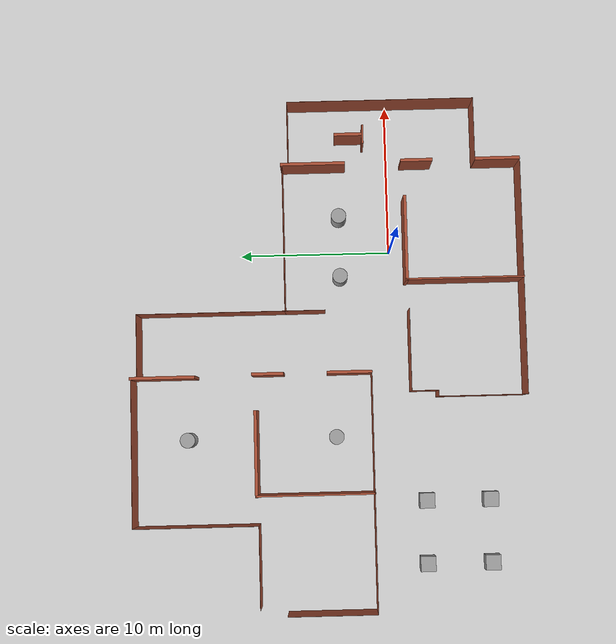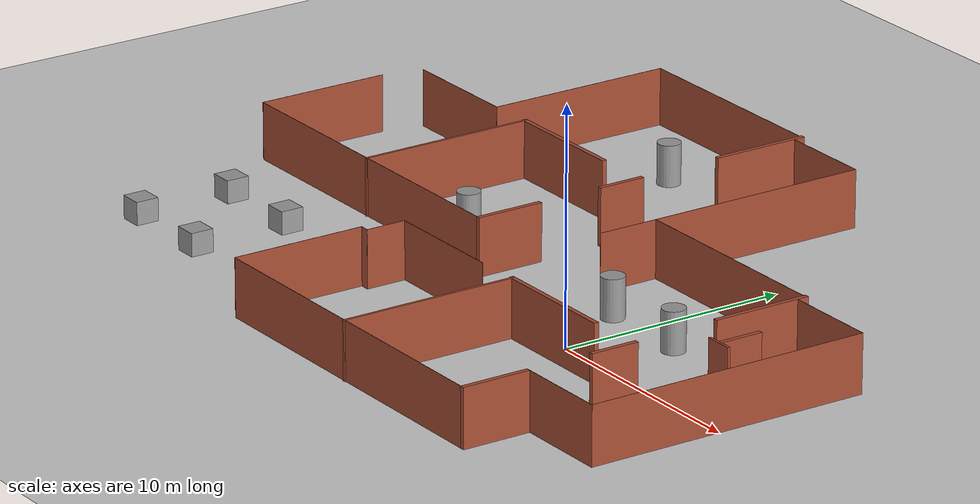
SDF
<sdf version="1.6">
 <world name="default">
  <light name="sun" type="directional">
   <pose>0 0 10 0 -0 0</pose>
   <diffuse>0.8 0.8 0.8 1</diffuse>
   <specular>0.1 0.1 0.1 1</specular>
   <attenuation>
    <range>1000</range>
    <constant>0.9</constant>
    <linear>0.01</linear>
    <quadratic>0.001</quadratic>
   </attenuation>
   <direction>-0.5 0.5 -1</direction>
  </light>
  <model name="ground_plane">
   <static>1</static>
   <link name="link">
    <collision name="collision">
     <geometry><plane><normal>0 0 1</normal><size>100 100</size></plane></geometry>
     <surface><friction><ode><mu>100</mu><mu2>50</mu2></ode></friction></surface>
    </collision>
    <visual name="visual">
     <cast_shadows>0</cast_shadows>
     <geometry><plane><normal>0 0 1</normal><size>100 100</size></plane></geometry>
     <material>
      <script><uri>file://media/materials/scripts/gazebo.material</uri><name>Gazebo/Grey</name></script>
     </material>
    </visual>
   </link>
  </model>
  <gravity>0 0 -9.8</gravity>
  <magnetic_field>6e-06 2.3e-05 -4.2e-05</magnetic_field>
  <atmosphere type="adiabatic"/>
  <physics name="default_physics" default="0" type="ode">
   <max_step_size>0.001</max_step_size>
   <real_time_factor>1</real_time_factor>
   <real_time_update_rate>1000</real_time_update_rate>
  </physics>
  <scene><ambient>0.4 0.4 0.4 1</ambient><background>0.7 0.7 0.7 1</background><shadows>1</shadows></scene>
  <spherical_coordinates>
   <surface_model>EARTH_WGS84</surface_model>
   <latitude_deg>0</latitude_deg>
   <longitude_deg>0</longitude_deg>
   <elevation>0</elevation>
   <heading_deg>0</heading_deg>
  </spherical_coordinates>
  <model name="ANPL_Lab_Extended_0_0">
   <link name="Wall_165">
    <pose>-9.925 -4.975 0 0 -0 1.5708</pose>
    <visual name="Wall_165_Visual">
     <pose>0 0 1.25 0 -0 0</pose>
     <geometry><box><size>5.86 0.01 2.5</size></box></geometry>
     <material>
      <script><uri>file://media/materials/scripts/gazebo.material</uri><name>Gazebo/Bricks</name></script>
      <ambient>0.435294 0.796078 0.67451 1</ambient>
      <diffuse>1 1 1 1</diffuse>
      <specular>0.2 0.2 0.2 1</specular>
      <emissive>0 0 0 1</emissive>
     </material>
    </visual>
    <collision name="Wall_165_Collision">
     <pose>0 0 1.25 0 -0 0</pose>
     <geometry><box><size>5.86 0.01 2.5</size></box></geometry>
     <surface>
      <friction>
       <ode><mu>1</mu><mu2>1</mu2><fdir1>0 0 0</fdir1><slip1>0</slip1><slip2>0</slip2></ode>
       <torsional>
        <coefficient>1</coefficient>
        <patch_radius>0</patch_radius>
        <surface_radius>0</surface_radius>
        <use_patch_radius>1</use_patch_radius>
        <ode><slip>0</slip></ode>
       </torsional>
      </friction>
      <bounce><restitution_coefficient>0</restitution_coefficient><threshold>1e+06</threshold></bounce>
      <contact>
       <collide_without_contact>0</collide_without_contact>
       <collide_without_contact_bitmask>1</collide_without_contact_bitmask>
       <collide_bitmask>1</collide_bitmask>
       <ode>
        <soft_cfm>0</soft_cfm>
        <soft_erp>0.2</soft_erp>
        <kp>1e+13</kp>
        <kd>1</kd>
        <max_vel>0.01</max_vel>
        <min_depth>0</min_depth>
       </ode>
       <bullet>
        <split_impulse>1</split_impulse>
        <split_impulse_penetration_threshold>-0.01</split_impulse_penetration_threshold>
        <soft_cfm>0</soft_cfm>
        <soft_erp>0.2</soft_erp>
        <kp>1e+13</kp>
        <kd>1</kd>
       </bullet>
      </contact>
     </surface>
    </collision>
   </link>
   <link name="Wall_167">
    <pose>-9.725 -2.05 0 0 -0 0</pose>
    <visual name="Wall_167_Visual">
     <pose>0 0 1.25 0 -0 0</pose>
     <geometry><box><size>0.41 0.01 2.5</size></box></geometry>
     <material>
      <script><uri>file://media/materials/scripts/gazebo.material</uri><name>Gazebo/Bricks</name></script>
      <ambient>0.435294 0.796078 0.67451 1</ambient>
      <diffuse>1 1 1 1</diffuse>
      <specular>0.2 0.2 0.2 1</specular>
      <emissive>0 0 0 1</emissive>
     </material>
    </visual>
    <collision name="Wall_167_Collision">
     <pose>0 0 1.25 0 -0 0</pose>
     <geometry><box><size>0.41 0.01 2.5</size></box></geometry>
     <surface>
      <friction>
       <ode><mu>1</mu><mu2>1</mu2><fdir1>0 0 0</fdir1><slip1>0</slip1><slip2>0</slip2></ode>
       <torsional>
        <coefficient>1</coefficient>
        <patch_radius>0</patch_radius>
        <surface_radius>0</surface_radius>
        <use_patch_radius>1</use_patch_radius>
        <ode><slip>0</slip></ode>
       </torsional>
      </friction>
      <bounce><restitution_coefficient>0</restitution_coefficient><threshold>1e+06</threshold></bounce>
      <contact>
       <collide_without_contact>0</collide_without_contact>
       <collide_without_contact_bitmask>1</collide_without_contact_bitmask>
       <collide_bitmask>1</collide_bitmask>
       <ode>
        <soft_cfm>0</soft_cfm>
        <soft_erp>0.2</soft_erp>
        <kp>1e+13</kp>
        <kd>1</kd>
        <max_vel>0.01</max_vel>
        <min_depth>0</min_depth>
       </ode>
       <bullet>
        <split_impulse>1</split_impulse>
        <split_impulse_penetration_threshold>-0.01</split_impulse_penetration_threshold>
        <soft_cfm>0</soft_cfm>
        <soft_erp>0.2</soft_erp>
        <kp>1e+13</kp>
        <kd>1</kd>
       </bullet>
      </contact>
     </surface>
    </collision>
   </link>
   <link name="Wall_169">
    <pose>-9.525 -1.175 0 0 -0 1.5708</pose>
    <visual name="Wall_169_Visual">
     <pose>0 0 1.25 0 -0 0</pose>
     <geometry><box><size>1.76 0.01 2.5</size></box></geometry>
     <material>
      <script><uri>file://media/materials/scripts/gazebo.material</uri><name>Gazebo/Bricks</name></script>
      <ambient>0.435294 0.796078 0.67451 1</ambient>
      <diffuse>1 1 1 1</diffuse>
      <specular>0.2 0.2 0.2 1</specular>
      <emissive>0 0 0 1</emissive>
     </material>
    </visual>
    <collision name="Wall_169_Collision">
     <pose>0 0 1.25 0 -0 0</pose>
     <geometry><box><size>1.76 0.01 2.5</size></box></geometry>
     <surface>
      <friction>
       <ode><mu>1</mu><mu2>1</mu2><fdir1>0 0 0</fdir1><slip1>0</slip1><slip2>0</slip2></ode>
       <torsional>
        <coefficient>1</coefficient>
        <patch_radius>0</patch_radius>
        <surface_radius>0</surface_radius>
        <use_patch_radius>1</use_patch_radius>
        <ode><slip>0</slip></ode>
       </torsional>
      </friction>
      <bounce><restitution_coefficient>0</restitution_coefficient><threshold>1e+06</threshold></bounce>
      <contact>
       <collide_without_contact>0</collide_without_contact>
       <collide_without_contact_bitmask>1</collide_without_contact_bitmask>
       <collide_bitmask>1</collide_bitmask>
       <ode>
        <soft_cfm>0</soft_cfm>
        <soft_erp>0.2</soft_erp>
        <kp>1e+13</kp>
        <kd>1</kd>
        <max_vel>0.01</max_vel>
        <min_depth>0</min_depth>
       </ode>
       <bullet>
        <split_impulse>1</split_impulse>
        <split_impulse_penetration_threshold>-0.01</split_impulse_penetration_threshold>
        <soft_cfm>0</soft_cfm>
        <soft_erp>0.2</soft_erp>
        <kp>1e+13</kp>
        <kd>1</kd>
       </bullet>
      </contact>
     </surface>
    </collision>
   </link>
   <link name="Wall_171">
    <pose>-6.8125 -0.3 0 0 -0 0</pose>
    <visual name="Wall_171_Visual">
     <pose>0 0 1.25 0 -0 0</pose>
     <geometry><box><size>5.435 0.01 2.5</size></box></geometry>
     <material>
      <script><uri>file://media/materials/scripts/gazebo.material</uri><name>Gazebo/Bricks</name></script>
      <ambient>0.435294 0.796078 0.67451 1</ambient>
      <diffuse>1 1 1 1</diffuse>
      <specular>0.2 0.2 0.2 1</specular>
      <emissive>0 0 0 1</emissive>
     </material>
    </visual>
    <collision name="Wall_171_Collision">
     <pose>0 0 1.25 0 -0 0</pose>
     <geometry><box><size>5.435 0.01 2.5</size></box></geometry>
     <surface>
      <friction>
       <ode><mu>1</mu><mu2>1</mu2><fdir1>0 0 0</fdir1><slip1>0</slip1><slip2>0</slip2></ode>
       <torsional>
        <coefficient>1</coefficient>
        <patch_radius>0</patch_radius>
        <surface_radius>0</surface_radius>
        <use_patch_radius>1</use_patch_radius>
        <ode><slip>0</slip></ode>
       </torsional>
      </friction>
      <bounce><restitution_coefficient>0</restitution_coefficient><threshold>1e+06</threshold></bounce>
      <contact>
       <collide_without_contact>0</collide_without_contact>
       <collide_without_contact_bitmask>1</collide_without_contact_bitmask>
       <collide_bitmask>1</collide_bitmask>
       <ode>
        <soft_cfm>0</soft_cfm>
        <soft_erp>0.2</soft_erp>
        <kp>1e+13</kp>
        <kd>1</kd>
        <max_vel>0.01</max_vel>
        <min_depth>0</min_depth>
       </ode>
       <bullet>
        <split_impulse>1</split_impulse>
        <split_impulse_penetration_threshold>-0.01</split_impulse_penetration_threshold>
        <soft_cfm>0</soft_cfm>
        <soft_erp>0.2</soft_erp>
        <kp>1e+13</kp>
        <kd>1</kd>
       </bullet>
      </contact>
     </surface>
    </collision>
   </link>
   <link name="Wall_175">
    <pose>0.7875 7.9 0 0 -0 0</pose>
    <visual name="Wall_175_Visual">
     <pose>0 0 1.25 0 -0 0</pose>
     <geometry><box><size>9.785 0.01 2.5</size></box></geometry>
     <material>
      <script><uri>file://media/materials/scripts/gazebo.material</uri><name>Gazebo/Bricks</name></script>
      <ambient>0.435294 0.796078 0.67451 1</ambient>
      <diffuse>1 1 1 1</diffuse>
      <specular>0.2 0.2 0.2 1</specular>
      <emissive>0 0 0 1</emissive>
     </material>
    </visual>
    <collision name="Wall_175_Collision">
     <pose>0 0 1.25 0 -0 0</pose>
     <geometry><box><size>9.785 0.01 2.5</size></box></geometry>
     <surface>
      <friction>
       <ode><mu>1</mu><mu2>1</mu2><fdir1>0 0 0</fdir1><slip1>0</slip1><slip2>0</slip2></ode>
       <torsional>
        <coefficient>1</coefficient>
        <patch_radius>0</patch_radius>
        <surface_radius>0</surface_radius>
        <use_patch_radius>1</use_patch_radius>
        <ode><slip>0</slip></ode>
       </torsional>
      </friction>
      <bounce><restitution_coefficient>0</restitution_coefficient><threshold>1e+06</threshold></bounce>
      <contact>
       <collide_without_contact>0</collide_without_contact>
       <collide_without_contact_bitmask>1</collide_without_contact_bitmask>
       <collide_bitmask>1</collide_bitmask>
       <ode>
        <soft_cfm>0</soft_cfm>
        <soft_erp>0.2</soft_erp>
        <kp>1e+13</kp>
        <kd>1</kd>
        <max_vel>0.01</max_vel>
        <min_depth>0</min_depth>
       </ode>
       <bullet>
        <split_impulse>1</split_impulse>
        <split_impulse_penetration_threshold>-0.01</split_impulse_penetration_threshold>
        <soft_cfm>0</soft_cfm>
        <soft_erp>0.2</soft_erp>
        <kp>1e+13</kp>
        <kd>1</kd>
       </bullet>
      </contact>
     </surface>
    </collision>
   </link>
   <link name="Wall_177">
    <pose>5.675 5.85 0 0 0 -1.5708</pose>
    <visual name="Wall_177_Visual">
     <pose>0 0 1.25 0 -0 0</pose>
     <geometry><box><size>4.3 0.2 2.5</size></box></geometry>
     <material>
      <script><uri>file://media/materials/scripts/gazebo.material</uri><name>Gazebo/Bricks</name></script>
      <ambient>0.435294 0.796078 0.67451 1</ambient>
      <diffuse>1 1 1 1</diffuse>
      <specular>0.2 0.2 0.2 1</specular>
      <emissive>0 0 0 1</emissive>
     </material>
    </visual>
    <collision name="Wall_177_Collision">
     <pose>0 0 1.25 0 -0 0</pose>
     <geometry><box><size>4.3 0.2 2.5</size></box></geometry>
     <surface>
      <friction>
       <ode><mu>1</mu><mu2>1</mu2><fdir1>0 0 0</fdir1><slip1>0</slip1><slip2>0</slip2></ode>
       <torsional>
        <coefficient>1</coefficient>
        <patch_radius>0</patch_radius>
        <surface_radius>0</surface_radius>
        <use_patch_radius>1</use_patch_radius>
        <ode><slip>0</slip></ode>
       </torsional>
      </friction>
      <bounce><restitution_coefficient>0</restitution_coefficient><threshold>1e+06</threshold></bounce>
      <contact>
       <collide_without_contact>0</collide_without_contact>
       <collide_without_contact_bitmask>1</collide_without_contact_bitmask>
       <collide_bitmask>1</collide_bitmask>
       <ode>
        <soft_cfm>0</soft_cfm>
        <soft_erp>0.2</soft_erp>
        <kp>1e+13</kp>
        <kd>1</kd>
        <max_vel>0.01</max_vel>
        <min_depth>0</min_depth>
       </ode>
       <bullet>
        <split_impulse>1</split_impulse>
        <split_impulse_penetration_threshold>-0.01</split_impulse_penetration_threshold>
        <soft_cfm>0</soft_cfm>
        <soft_erp>0.2</soft_erp>
        <kp>1e+13</kp>
        <kd>1</kd>
       </bullet>
      </contact>
     </surface>
    </collision>
   </link>
   <link name="Wall_179">
    <pose>7.775 7.5 0 0 -0 0</pose>
    <visual name="Wall_179_Visual">
     <pose>0 0 1.25 0 -0 0</pose>
     <geometry><box><size>4.21 0.01 2.5</size></box></geometry>
     <material>
      <script><uri>file://media/materials/scripts/gazebo.material</uri><name>Gazebo/Bricks</name></script>
      <ambient>0.435294 0.796078 0.67451 1</ambient>
      <diffuse>1 1 1 1</diffuse>
      <specular>0.2 0.2 0.2 1</specular>
      <emissive>0 0 0 1</emissive>
     </material>
    </visual>
    <collision name="Wall_179_Collision">
     <pose>0 0 1.25 0 -0 0</pose>
     <geometry><box><size>4.21 0.01 2.5</size></box></geometry>
     <surface>
      <friction>
       <ode><mu>1</mu><mu2>1</mu2><fdir1>0 0 0</fdir1><slip1>0</slip1><slip2>0</slip2></ode>
       <torsional>
        <coefficient>1</coefficient>
        <patch_radius>0</patch_radius>
        <surface_radius>0</surface_radius>
        <use_patch_radius>1</use_patch_radius>
        <ode><slip>0</slip></ode>
       </torsional>
      </friction>
      <bounce><restitution_coefficient>0</restitution_coefficient><threshold>1e+06</threshold></bounce>
      <contact>
       <collide_without_contact>0</collide_without_contact>
       <collide_without_contact_bitmask>1</collide_without_contact_bitmask>
       <collide_bitmask>1</collide_bitmask>
       <ode>
        <soft_cfm>0</soft_cfm>
        <soft_erp>0.2</soft_erp>
        <kp>1e+13</kp>
        <kd>1</kd>
        <max_vel>0.01</max_vel>
        <min_depth>0</min_depth>
       </ode>
       <bullet>
        <split_impulse>1</split_impulse>
        <split_impulse_penetration_threshold>-0.01</split_impulse_penetration_threshold>
        <soft_cfm>0</soft_cfm>
        <soft_erp>0.2</soft_erp>
        <kp>1e+13</kp>
        <kd>1</kd>
       </bullet>
      </contact>
     </surface>
    </collision>
   </link>
   <link name="Wall_181">
    <pose>9.875 1.285 0 0 0 -1.5708</pose>
    <visual name="Wall_181_Visual">
     <pose>0 0 1.25 0 -0 0</pose>
     <geometry><box><size>12.44 0.01 2.5</size></box></geometry>
     <material>
      <script><uri>file://media/materials/scripts/gazebo.material</uri><name>Gazebo/Bricks</name></script>
      <ambient>0.435294 0.796078 0.67451 1</ambient>
      <diffuse>1 1 1 1</diffuse>
      <specular>0.2 0.2 0.2 1</specular>
      <emissive>0 0 0 1</emissive>
     </material>
    </visual>
    <collision name="Wall_181_Collision">
     <pose>0 0 1.25 0 -0 0</pose>
     <geometry><box><size>12.44 0.01 2.5</size></box></geometry>
     <surface>
      <friction>
       <ode><mu>1</mu><mu2>1</mu2><fdir1>0 0 0</fdir1><slip1>0</slip1><slip2>0</slip2></ode>
       <torsional>
        <coefficient>1</coefficient>
        <patch_radius>0</patch_radius>
        <surface_radius>0</surface_radius>
        <use_patch_radius>1</use_patch_radius>
        <ode><slip>0</slip></ode>
       </torsional>
      </friction>
      <bounce><restitution_coefficient>0</restitution_coefficient><threshold>1e+06</threshold></bounce>
      <contact>
       <collide_without_contact>0</collide_without_contact>
       <collide_without_contact_bitmask>1</collide_without_contact_bitmask>
       <collide_bitmask>1</collide_bitmask>
       <ode>
        <soft_cfm>0</soft_cfm>
        <soft_erp>0.2</soft_erp>
        <kp>1e+13</kp>
        <kd>1</kd>
        <max_vel>0.01</max_vel>
        <min_depth>0</min_depth>
       </ode>
       <bullet>
        <split_impulse>1</split_impulse>
        <split_impulse_penetration_threshold>-0.01</split_impulse_penetration_threshold>
        <soft_cfm>0</soft_cfm>
        <soft_erp>0.2</soft_erp>
        <kp>1e+13</kp>
        <kd>1</kd>
       </bullet>
      </contact>
     </surface>
    </collision>
   </link>
   <link name="Wall_183">
    <pose>7.6044 3.46126 0 0 -0 1.5708</pose>
    <inertial>
     <mass>1.43571</mass>
     <inertia><ixx>1.43571</ixx><ixy>0</ixy><ixz>0</ixz><iyy>2.19753</iyy><iyz>0</iyz><izz>2.19753</izz></inertia>
    </inertial>
    <visual name="Wall_183_Visual">
     <pose>0 0 1.25 0 -0 0</pose>
     <geometry><box><size>1.86641 0.2 2.5</size></box></geometry>
     <material>
      <script><uri>file://media/materials/scripts/gazebo.material</uri><name>Gazebo/Bricks</name></script>
      <ambient>0.435 0.796 0.675 1</ambient>
      <diffuse>1 1 1 1</diffuse>
      <specular>0.2 0.2 0.2 1</specular>
      <emissive>0 0 0 1</emissive>
      <shader type="vertex"><normal_map>__default__</normal_map></shader>
     </material>
    </visual>
    <collision name="Wall_183_Collision">
     <pose>0 0 1.25 0 -0 0</pose>
     <geometry><box><size>1.86641 0.2 2.5</size></box></geometry>
     <surface>
      <friction>
       <ode><mu>1</mu><mu2>1</mu2><fdir1>0 0 0</fdir1><slip1>0</slip1><slip2>0</slip2></ode>
       <torsional>
        <coefficient>1</coefficient>
        <patch_radius>0</patch_radius>
        <surface_radius>0</surface_radius>
        <use_patch_radius>1</use_patch_radius>
        <ode><slip>0</slip></ode>
       </torsional>
      </friction>
      <bounce><restitution_coefficient>0</restitution_coefficient><threshold>1e+06</threshold></bounce>
      <contact>
       <collide_without_contact>0</collide_without_contact>
       <collide_without_contact_bitmask>1</collide_without_contact_bitmask>
       <collide_bitmask>1</collide_bitmask>
       <ode>
        <soft_cfm>0</soft_cfm>
        <soft_erp>0.2</soft_erp>
        <kp>1e+13</kp>
        <kd>1</kd>
        <max_vel>0.01</max_vel>
        <min_depth>0</min_depth>
       </ode>
       <bullet>
        <split_impulse>1</split_impulse>
        <split_impulse_penetration_threshold>-0.01</split_impulse_penetration_threshold>
        <soft_cfm>0</soft_cfm>
        <soft_erp>0.2</soft_erp>
        <kp>1e+13</kp>
        <kd>1</kd>
       </bullet>
      </contact>
     </surface>
    </collision>
   </link>
   <link name="Wall_185">
    <pose>5.76868 -1.05 0 0 0 -1.5708</pose>
    <inertial>
     <mass>1</mass>
     <inertia><ixx>1</ixx><ixy>0</ixy><ixz>0</ixz><iyy>1</iyy><iyz>0</iyz><izz>1</izz></inertia>
    </inertial>
    <visual name="Wall_185_Visual">
     <pose>0 0 1.25 0 -0 0</pose>
     <geometry><box><size>2.1 0.2 2.5</size></box></geometry>
     <material>
      <script><uri>file://media/materials/scripts/gazebo.material</uri><name>Gazebo/Bricks</name></script>
      <ambient>0.435 0.796 0.675 1</ambient>
      <diffuse>1 1 1 1</diffuse>
      <specular>0.2 0.2 0.2 1</specular>
      <emissive>0 0 0 1</emissive>
      <shader type="vertex"><normal_map>__default__</normal_map></shader>
     </material>
    </visual>
    <collision name="Wall_185_Collision">
     <pose>0 0 1.25 0 -0 0</pose>
     <geometry><box><size>2.1 0.2 2.5</size></box></geometry>
     <surface>
      <friction>
       <ode><mu>1</mu><mu2>1</mu2><fdir1>0 0 0</fdir1><slip1>0</slip1><slip2>0</slip2></ode>
       <torsional>
        <coefficient>1</coefficient>
        <patch_radius>0</patch_radius>
        <surface_radius>0</surface_radius>
        <use_patch_radius>1</use_patch_radius>
        <ode><slip>0</slip></ode>
       </torsional>
      </friction>
      <bounce><restitution_coefficient>0</restitution_coefficient><threshold>1e+06</threshold></bounce>
      <contact>
       <collide_without_contact>0</collide_without_contact>
       <collide_without_contact_bitmask>1</collide_without_contact_bitmask>
       <collide_bitmask>1</collide_bitmask>
       <ode>
        <soft_cfm>0</soft_cfm>
        <soft_erp>0.2</soft_erp>
        <kp>1e+13</kp>
        <kd>1</kd>
        <max_vel>0.01</max_vel>
        <min_depth>0</min_depth>
       </ode>
       <bullet>
        <split_impulse>1</split_impulse>
        <split_impulse_penetration_threshold>-0.01</split_impulse_penetration_threshold>
        <soft_cfm>0</soft_cfm>
        <soft_erp>0.2</soft_erp>
        <kp>1e+13</kp>
        <kd>1</kd>
       </bullet>
      </contact>
     </surface>
    </collision>
   </link>
   <link name="Wall_187">
    <pose>7.59405 2.49 0 0 -0 0</pose>
    <inertial>
     <inertia><ixx>nan</ixx><ixy>0</ixy><ixz>0</ixz><iyy>nan</iyy><iyz>0</iyz><izz>nan</izz></inertia>
     <mass>0</mass>
    </inertial>
    <visual name="Wall_187_Visual">
     <pose>0 0 1.25 0 -0 0</pose>
     <geometry><box><size>1.23163 0.11 2.5</size></box></geometry>
     <material>
      <script><uri>file://media/materials/scripts/gazebo.material</uri><name>Gazebo/Bricks</name></script>
      <ambient>0.435294 0.796078 0.67451 1</ambient>
      <diffuse>1 1 1 1</diffuse>
      <specular>0.2 0.2 0.2 1</specular>
      <emissive>0 0 0 1</emissive>
     </material>
    </visual>
    <collision name="Wall_187_Collision">
     <pose>0 0 1.25 0 -0 0</pose>
     <geometry><box><size>1.23163 0.11 2.5</size></box></geometry>
     <surface>
      <friction>
       <ode><mu>1</mu><mu2>1</mu2><fdir1>0 0 0</fdir1><slip1>0</slip1><slip2>0</slip2></ode>
       <torsional>
        <coefficient>1</coefficient>
        <patch_radius>0</patch_radius>
        <surface_radius>0</surface_radius>
        <use_patch_radius>1</use_patch_radius>
        <ode><slip>0</slip></ode>
       </torsional>
      </friction>
      <bounce><restitution_coefficient>0</restitution_coefficient><threshold>1e+06</threshold></bounce>
      <contact>
       <collide_without_contact>0</collide_without_contact>
       <collide_without_contact_bitmask>1</collide_without_contact_bitmask>
       <collide_bitmask>1</collide_bitmask>
       <ode>
        <soft_cfm>0</soft_cfm>
        <soft_erp>0.2</soft_erp>
        <kp>1e+13</kp>
        <kd>1</kd>
        <max_vel>0.01</max_vel>
        <min_depth>0</min_depth>
       </ode>
       <bullet>
        <split_impulse>1</split_impulse>
        <split_impulse_penetration_threshold>-0.01</split_impulse_penetration_threshold>
        <soft_cfm>0</soft_cfm>
        <soft_erp>0.2</soft_erp>
        <kp>1e+13</kp>
        <kd>1</kd>
       </bullet>
      </contact>
     </surface>
    </collision>
   </link>
   <link name="Wall_201">
    <pose>7.775 -4.93 0 0 -0 3.14159</pose>
    <visual name="Wall_201_Visual">
     <pose>0 0 1.25 0 -0 0</pose>
     <geometry><box><size>4.21 0.01 2.5</size></box></geometry>
     <material>
      <script><uri>file://media/materials/scripts/gazebo.material</uri><name>Gazebo/Bricks</name></script>
      <ambient>0.435294 0.796078 0.67451 1</ambient>
      <diffuse>1 1 1 1</diffuse>
      <specular>0.2 0.2 0.2 1</specular>
      <emissive>0 0 0 1</emissive>
     </material>
    </visual>
    <collision name="Wall_201_Collision">
     <pose>0 0 1.25 0 -0 0</pose>
     <geometry><box><size>4.21 0.01 2.5</size></box></geometry>
     <surface>
      <friction>
       <ode><mu>1</mu><mu2>1</mu2><fdir1>0 0 0</fdir1><slip1>0</slip1><slip2>0</slip2></ode>
       <torsional>
        <coefficient>1</coefficient>
        <patch_radius>0</patch_radius>
        <surface_radius>0</surface_radius>
        <use_patch_radius>1</use_patch_radius>
        <ode><slip>0</slip></ode>
       </torsional>
      </friction>
      <bounce><restitution_coefficient>0</restitution_coefficient><threshold>1e+06</threshold></bounce>
      <contact>
       <collide_without_contact>0</collide_without_contact>
       <collide_without_contact_bitmask>1</collide_without_contact_bitmask>
       <collide_bitmask>1</collide_bitmask>
       <ode>
        <soft_cfm>0</soft_cfm>
        <soft_erp>0.2</soft_erp>
        <kp>1e+13</kp>
        <kd>1</kd>
        <max_vel>0.01</max_vel>
        <min_depth>0</min_depth>
       </ode>
       <bullet>
        <split_impulse>1</split_impulse>
        <split_impulse_penetration_threshold>-0.01</split_impulse_penetration_threshold>
        <soft_cfm>0</soft_cfm>
        <soft_erp>0.2</soft_erp>
        <kp>1e+13</kp>
        <kd>1</kd>
       </bullet>
      </contact>
     </surface>
    </collision>
   </link>
   <link name="Wall_203">
    <pose>5.76868 -6.42951 0 0 0 -1.5708</pose>
    <inertial>
     <inertia>
      <ixx>1.79769e+308</ixx>
      <ixy>0</ixy>
      <ixz>0</ixz>
      <iyy>1.79769e+308</iyy>
      <iyz>0</iyz>
      <izz>1.79769e+308</izz>
     </inertia>
     <mass>0</mass>
    </inertial>
    <visual name="Wall_203_Visual">
     <pose>0 0 1.25 0 -0 0</pose>
     <geometry><box><size>2.97075 0.2 2.5</size></box></geometry>
     <material>
      <script><uri>file://media/materials/scripts/gazebo.material</uri><name>Gazebo/Bricks</name></script>
      <ambient>0.435 0.796 0.675 1</ambient>
      <diffuse>1 1 1 1</diffuse>
      <specular>0.2 0.2 0.2 1</specular>
      <emissive>0 0 0 1</emissive>
      <shader type="vertex"><normal_map>__default__</normal_map></shader>
     </material>
    </visual>
    <collision name="Wall_203_Collision">
     <pose>0 0 1.25 0 -0 0</pose>
     <geometry><box><size>2.97075 0.2 2.5</size></box></geometry>
     <surface>
      <friction>
       <ode><mu>1</mu><mu2>1</mu2><fdir1>0 0 0</fdir1><slip1>0</slip1><slip2>0</slip2></ode>
       <torsional>
        <coefficient>1</coefficient>
        <patch_radius>0</patch_radius>
        <surface_radius>0</surface_radius>
        <use_patch_radius>1</use_patch_radius>
        <ode><slip>0</slip></ode>
       </torsional>
      </friction>
      <bounce><restitution_coefficient>0</restitution_coefficient><threshold>1e+06</threshold></bounce>
      <contact>
       <collide_without_contact>0</collide_without_contact>
       <collide_without_contact_bitmask>1</collide_without_contact_bitmask>
       <collide_bitmask>1</collide_bitmask>
       <ode>
        <soft_cfm>0</soft_cfm>
        <soft_erp>0.2</soft_erp>
        <kp>1e+13</kp>
        <kd>1</kd>
        <max_vel>0.01</max_vel>
        <min_depth>0</min_depth>
       </ode>
       <bullet>
        <split_impulse>1</split_impulse>
        <split_impulse_penetration_threshold>-0.01</split_impulse_penetration_threshold>
        <soft_cfm>0</soft_cfm>
        <soft_erp>0.2</soft_erp>
        <kp>1e+13</kp>
        <kd>1</kd>
       </bullet>
      </contact>
     </surface>
    </collision>
   </link>
   <link name="Wall_205">
    <pose>-2.125 -7.9 0 0 -0 3.14159</pose>
    <visual name="Wall_205_Visual">
     <pose>0 0 1.25 0 -0 0</pose>
     <geometry><box><size>15.61 0.01 2.5</size></box></geometry>
     <material>
      <script><uri>file://media/materials/scripts/gazebo.material</uri><name>Gazebo/Bricks</name></script>
      <ambient>0.435294 0.796078 0.67451 1</ambient>
      <diffuse>1 1 1 1</diffuse>
      <specular>0.2 0.2 0.2 1</specular>
      <emissive>0 0 0 1</emissive>
     </material>
    </visual>
    <collision name="Wall_205_Collision">
     <pose>0 0 1.25 0 -0 0</pose>
     <geometry><box><size>15.61 0.01 2.5</size></box></geometry>
     <surface>
      <friction>
       <ode><mu>1</mu><mu2>1</mu2><fdir1>0 0 0</fdir1><slip1>0</slip1><slip2>0</slip2></ode>
       <torsional>
        <coefficient>1</coefficient>
        <patch_radius>0</patch_radius>
        <surface_radius>0</surface_radius>
        <use_patch_radius>1</use_patch_radius>
        <ode><slip>0</slip></ode>
       </torsional>
      </friction>
      <bounce><restitution_coefficient>0</restitution_coefficient><threshold>1e+06</threshold></bounce>
      <contact>
       <collide_without_contact>0</collide_without_contact>
       <collide_without_contact_bitmask>1</collide_without_contact_bitmask>
       <collide_bitmask>1</collide_bitmask>
       <ode>
        <soft_cfm>0</soft_cfm>
        <soft_erp>0.2</soft_erp>
        <kp>1e+13</kp>
        <kd>1</kd>
        <max_vel>0.01</max_vel>
        <min_depth>0</min_depth>
       </ode>
       <bullet>
        <split_impulse>1</split_impulse>
        <split_impulse_penetration_threshold>-0.01</split_impulse_penetration_threshold>
        <soft_cfm>0</soft_cfm>
        <soft_erp>0.2</soft_erp>
        <kp>1e+13</kp>
        <kd>1</kd>
       </bullet>
      </contact>
     </surface>
    </collision>
   </link>
   <link name="Wall_207">
    <pose>-2.175 -4.05 0 0 -0 1.5708</pose>
    <visual name="Wall_207_Visual">
     <pose>0 0 1.25 0 -0 0</pose>
     <geometry><box><size>7.81 0.11 2.5</size></box></geometry>
     <material>
      <script><uri>file://media/materials/scripts/gazebo.material</uri><name>Gazebo/Bricks</name></script>
      <ambient>0.435294 0.796078 0.67451 1</ambient>
      <diffuse>1 1 1 1</diffuse>
      <specular>0.2 0.2 0.2 1</specular>
      <emissive>0 0 0 1</emissive>
     </material>
    </visual>
    <collision name="Wall_207_Collision">
     <pose>0 0 1.25 0 -0 0</pose>
     <geometry><box><size>7.81 0.11 2.5</size></box></geometry>
     <surface>
      <friction>
       <ode><mu>1</mu><mu2>1</mu2><fdir1>0 0 0</fdir1><slip1>0</slip1><slip2>0</slip2></ode>
       <torsional>
        <coefficient>1</coefficient>
        <patch_radius>0</patch_radius>
        <surface_radius>0</surface_radius>
        <use_patch_radius>1</use_patch_radius>
        <ode><slip>0</slip></ode>
       </torsional>
      </friction>
      <bounce><restitution_coefficient>0</restitution_coefficient><threshold>1e+06</threshold></bounce>
      <contact>
       <collide_without_contact>0</collide_without_contact>
       <collide_without_contact_bitmask>1</collide_without_contact_bitmask>
       <collide_bitmask>1</collide_bitmask>
       <ode>
        <soft_cfm>0</soft_cfm>
        <soft_erp>0.2</soft_erp>
        <kp>1e+13</kp>
        <kd>1</kd>
        <max_vel>0.01</max_vel>
        <min_depth>0</min_depth>
       </ode>
       <bullet>
        <split_impulse>1</split_impulse>
        <split_impulse_penetration_threshold>-0.01</split_impulse_penetration_threshold>
        <soft_cfm>0</soft_cfm>
        <soft_erp>0.2</soft_erp>
        <kp>1e+13</kp>
        <kd>1</kd>
       </bullet>
      </contact>
     </surface>
    </collision>
   </link>
   <link name="Wall_209">
    <pose>0.571 -0.2 0 0 -0 0</pose>
    <inertial>
     <mass>1</mass>
     <inertia><ixx>1</ixx><ixy>0</ixy><ixz>0</ixz><iyy>1</iyy><iyz>0</iyz><izz>1</izz></inertia>
    </inertial>
    <visual name="Wall_209_Visual">
     <pose>0 0 1.25 0 -0 0</pose>
     <geometry><box><size>5.692 0.2 2.5</size></box></geometry>
     <material>
      <script><uri>file://media/materials/scripts/gazebo.material</uri><name>Gazebo/Bricks</name></script>
      <ambient>0.435 0.796 0.675 1</ambient>
      <diffuse>1 1 1 1</diffuse>
      <specular>0.2 0.2 0.2 1</specular>
      <emissive>0 0 0 1</emissive>
      <shader type="vertex"><normal_map>__default__</normal_map></shader>
     </material>
    </visual>
    <collision name="Wall_209_Collision">
     <pose>0 0 1.25 0 -0 0</pose>
     <geometry><box><size>5.692 0.2 2.5</size></box></geometry>
     <surface>
      <friction>
       <ode><mu>1</mu><mu2>1</mu2><fdir1>0 0 0</fdir1><slip1>0</slip1><slip2>0</slip2></ode>
       <torsional>
        <coefficient>1</coefficient>
        <patch_radius>0</patch_radius>
        <surface_radius>0</surface_radius>
        <use_patch_radius>1</use_patch_radius>
        <ode><slip>0</slip></ode>
       </torsional>
      </friction>
      <bounce><restitution_coefficient>0</restitution_coefficient><threshold>1e+06</threshold></bounce>
      <contact>
       <collide_without_contact>0</collide_without_contact>
       <collide_without_contact_bitmask>1</collide_without_contact_bitmask>
       <collide_bitmask>1</collide_bitmask>
       <ode>
        <soft_cfm>0</soft_cfm>
        <soft_erp>0.2</soft_erp>
        <kp>1e+13</kp>
        <kd>1</kd>
        <max_vel>0.01</max_vel>
        <min_depth>0</min_depth>
       </ode>
       <bullet>
        <split_impulse>1</split_impulse>
        <split_impulse_penetration_threshold>-0.01</split_impulse_penetration_threshold>
        <soft_cfm>0</soft_cfm>
        <soft_erp>0.2</soft_erp>
        <kp>1e+13</kp>
        <kd>1</kd>
       </bullet>
      </contact>
     </surface>
    </collision>
   </link>
   <link name="link_0">
    <pose>2.28416 4.2 0.5 0 -0 0</pose>
    <inertial>
     <mass>1</mass>
     <inertia><ixx>0.145833</ixx><ixy>0</ixy><ixz>0</ixz><iyy>0.145833</iyy><iyz>0</iyz><izz>0.125</izz></inertia>
    </inertial>
    <visual name="visual">
     <geometry><cylinder><radius>0.5</radius><length>2.5</length></cylinder></geometry>
     <material>
      <lighting>1</lighting>
      <script><uri>file://media/materials/scripts/gazebo.material</uri><name>Gazebo/Grey</name></script>
      <ambient>0.3 0.3 0.3 1</ambient>
      <diffuse>0.7 0.7 0.7 1</diffuse>
      <specular>0.01 0.01 0.01 1</specular>
      <emissive>0 0 0 1</emissive>
      <shader type="vertex"><normal_map>__default__</normal_map></shader>
     </material>
    </visual>
    <collision name="collision">
     <geometry><cylinder><radius>0.5</radius><length>2.5</length></cylinder></geometry>
     <surface>
      <friction>
       <ode><mu>1</mu><mu2>1</mu2><fdir1>0 0 0</fdir1><slip1>0</slip1><slip2>0</slip2></ode>
       <torsional>
        <coefficient>1</coefficient>
        <patch_radius>0</patch_radius>
        <surface_radius>0</surface_radius>
        <use_patch_radius>1</use_patch_radius>
        <ode><slip>0</slip></ode>
       </torsional>
      </friction>
      <bounce><restitution_coefficient>0</restitution_coefficient><threshold>1e+06</threshold></bounce>
      <contact>
       <collide_without_contact>0</collide_without_contact>
       <collide_without_contact_bitmask>1</collide_without_contact_bitmask>
       <collide_bitmask>1</collide_bitmask>
       <ode>
        <soft_cfm>0</soft_cfm>
        <soft_erp>0.2</soft_erp>
        <kp>1e+13</kp>
        <kd>1</kd>
        <max_vel>0.01</max_vel>
        <min_depth>0</min_depth>
       </ode>
       <bullet>
        <split_impulse>1</split_impulse>
        <split_impulse_penetration_threshold>-0.01</split_impulse_penetration_threshold>
        <soft_cfm>0</soft_cfm>
        <soft_erp>0.2</soft_erp>
        <kp>1e+13</kp>
        <kd>1</kd>
       </bullet>
      </contact>
     </surface>
    </collision>
   </link>
   <link name="link_1">
    <pose>-1.74778 4.2 0.5 0 -0 0</pose>
    <inertial>
     <mass>1</mass>
     <inertia><ixx>0.145833</ixx><ixy>0</ixy><ixz>0</ixz><iyy>0.145833</iyy><iyz>0</iyz><izz>0.125</izz></inertia>
    </inertial>
    <visual name="visual">
     <geometry><cylinder><radius>0.5</radius><length>2.5</length></cylinder></geometry>
     <material>
      <lighting>1</lighting>
      <script><uri>file://media/materials/scripts/gazebo.material</uri><name>Gazebo/Grey</name></script>
      <ambient>0.3 0.3 0.3 1</ambient>
      <diffuse>0.7 0.7 0.7 1</diffuse>
      <specular>0.01 0.01 0.01 1</specular>
      <emissive>0 0 0 1</emissive>
      <shader type="vertex"><normal_map>__default__</normal_map></shader>
     </material>
    </visual>
    <collision name="collision">
     <geometry><cylinder><radius>0.5</radius><length>2.5</length></cylinder></geometry>
     <surface>
      <friction>
       <ode><mu>1</mu><mu2>1</mu2><fdir1>0 0 0</fdir1><slip1>0</slip1><slip2>0</slip2></ode>
       <torsional>
        <coefficient>1</coefficient>
        <patch_radius>0</patch_radius>
        <surface_radius>0</surface_radius>
        <use_patch_radius>1</use_patch_radius>
        <ode><slip>0</slip></ode>
       </torsional>
      </friction>
      <bounce><restitution_coefficient>0</restitution_coefficient><threshold>1e+06</threshold></bounce>
      <contact>
       <collide_without_contact>0</collide_without_contact>
       <collide_without_contact_bitmask>1</collide_without_contact_bitmask>
       <collide_bitmask>1</collide_bitmask>
       <ode>
        <soft_cfm>0</soft_cfm>
        <soft_erp>0.2</soft_erp>
        <kp>1e+13</kp>
        <kd>1</kd>
        <max_vel>0.01</max_vel>
        <min_depth>0</min_depth>
       </ode>
       <bullet>
        <split_impulse>1</split_impulse>
        <split_impulse_penetration_threshold>-0.01</split_impulse_penetration_threshold>
        <soft_cfm>0</soft_cfm>
        <soft_erp>0.2</soft_erp>
        <kp>1e+13</kp>
        <kd>1</kd>
       </bullet>
      </contact>
     </surface>
    </collision>
   </link>
   <static>1</static>
   <pose>0.079097 -0.839942 0 0 -0 0</pose>
  </model>
  <model name="ANPL_Lab_Extended_1_0">
   <link name="Wall_165">
    <pose>-9.925 -4.975 0 0 -0 1.5708</pose>
    <visual name="Wall_165_Visual">
     <pose>0 0 1.25 0 -0 0</pose>
     <geometry><box><size>5.86 0.01 2.5</size></box></geometry>
     <material>
      <script><uri>file://media/materials/scripts/gazebo.material</uri><name>Gazebo/Bricks</name></script>
      <ambient>0.435294 0.796078 0.67451 1</ambient>
      <diffuse>1 1 1 1</diffuse>
      <specular>0.2 0.2 0.2 1</specular>
      <emissive>0 0 0 1</emissive>
     </material>
    </visual>
    <collision name="Wall_165_Collision">
     <pose>0 0 1.25 0 -0 0</pose>
     <geometry><box><size>5.86 0.01 2.5</size></box></geometry>
     <surface>
      <friction>
       <ode><mu>1</mu><mu2>1</mu2><fdir1>0 0 0</fdir1><slip1>0</slip1><slip2>0</slip2></ode>
       <torsional>
        <coefficient>1</coefficient>
        <patch_radius>0</patch_radius>
        <surface_radius>0</surface_radius>
        <use_patch_radius>1</use_patch_radius>
        <ode><slip>0</slip></ode>
       </torsional>
      </friction>
      <bounce><restitution_coefficient>0</restitution_coefficient><threshold>1e+06</threshold></bounce>
      <contact>
       <collide_without_contact>0</collide_without_contact>
       <collide_without_contact_bitmask>1</collide_without_contact_bitmask>
       <collide_bitmask>1</collide_bitmask>
       <ode>
        <soft_cfm>0</soft_cfm>
        <soft_erp>0.2</soft_erp>
        <kp>1e+13</kp>
        <kd>1</kd>
        <max_vel>0.01</max_vel>
        <min_depth>0</min_depth>
       </ode>
       <bullet>
        <split_impulse>1</split_impulse>
        <split_impulse_penetration_threshold>-0.01</split_impulse_penetration_threshold>
        <soft_cfm>0</soft_cfm>
        <soft_erp>0.2</soft_erp>
        <kp>1e+13</kp>
        <kd>1</kd>
       </bullet>
      </contact>
     </surface>
    </collision>
   </link>
   <link name="Wall_171">
    <pose>-6.8125 -0.3 0 0 -0 0</pose>
    <visual name="Wall_171_Visual">
     <pose>0 0 1.25 0 -0 0</pose>
     <geometry><box><size>5.435 0.01 2.5</size></box></geometry>
     <material>
      <script><uri>file://media/materials/scripts/gazebo.material</uri><name>Gazebo/Bricks</name></script>
      <ambient>0.435294 0.796078 0.67451 1</ambient>
      <diffuse>1 1 1 1</diffuse>
      <specular>0.2 0.2 0.2 1</specular>
      <emissive>0 0 0 1</emissive>
     </material>
    </visual>
    <collision name="Wall_171_Collision">
     <pose>0 0 1.25 0 -0 0</pose>
     <geometry><box><size>5.435 0.01 2.5</size></box></geometry>
     <surface>
      <friction>
       <ode><mu>1</mu><mu2>1</mu2><fdir1>0 0 0</fdir1><slip1>0</slip1><slip2>0</slip2></ode>
       <torsional>
        <coefficient>1</coefficient>
        <patch_radius>0</patch_radius>
        <surface_radius>0</surface_radius>
        <use_patch_radius>1</use_patch_radius>
        <ode><slip>0</slip></ode>
       </torsional>
      </friction>
      <bounce><restitution_coefficient>0</restitution_coefficient><threshold>1e+06</threshold></bounce>
      <contact>
       <collide_without_contact>0</collide_without_contact>
       <collide_without_contact_bitmask>1</collide_without_contact_bitmask>
       <collide_bitmask>1</collide_bitmask>
       <ode>
        <soft_cfm>0</soft_cfm>
        <soft_erp>0.2</soft_erp>
        <kp>1e+13</kp>
        <kd>1</kd>
        <max_vel>0.01</max_vel>
        <min_depth>0</min_depth>
       </ode>
       <bullet>
        <split_impulse>1</split_impulse>
        <split_impulse_penetration_threshold>-0.01</split_impulse_penetration_threshold>
        <soft_cfm>0</soft_cfm>
        <soft_erp>0.2</soft_erp>
        <kp>1e+13</kp>
        <kd>1</kd>
       </bullet>
      </contact>
     </surface>
    </collision>
   </link>
   <link name="Wall_173">
    <pose>-4.1 3.8 0 0 -0 1.5708</pose>
    <visual name="Wall_173_Visual">
     <pose>0 0 1.25 0 -0 0</pose>
     <geometry><box><size>8.21 0.01 2.5</size></box></geometry>
     <material>
      <script><uri>file://media/materials/scripts/gazebo.material</uri><name>Gazebo/Bricks</name></script>
      <ambient>0.435294 0.796078 0.67451 1</ambient>
      <diffuse>1 1 1 1</diffuse>
      <specular>0.2 0.2 0.2 1</specular>
      <emissive>0 0 0 1</emissive>
     </material>
    </visual>
    <collision name="Wall_173_Collision">
     <pose>0 0 1.25 0 -0 0</pose>
     <geometry><box><size>8.21 0.01 2.5</size></box></geometry>
     <surface>
      <friction>
       <ode><mu>1</mu><mu2>1</mu2><fdir1>0 0 0</fdir1><slip1>0</slip1><slip2>0</slip2></ode>
       <torsional>
        <coefficient>1</coefficient>
        <patch_radius>0</patch_radius>
        <surface_radius>0</surface_radius>
        <use_patch_radius>1</use_patch_radius>
        <ode><slip>0</slip></ode>
       </torsional>
      </friction>
      <bounce><restitution_coefficient>0</restitution_coefficient><threshold>1e+06</threshold></bounce>
      <contact>
       <collide_without_contact>0</collide_without_contact>
       <collide_without_contact_bitmask>1</collide_without_contact_bitmask>
       <collide_bitmask>1</collide_bitmask>
       <ode>
        <soft_cfm>0</soft_cfm>
        <soft_erp>0.2</soft_erp>
        <kp>1e+13</kp>
        <kd>1</kd>
        <max_vel>0.01</max_vel>
        <min_depth>0</min_depth>
       </ode>
       <bullet>
        <split_impulse>1</split_impulse>
        <split_impulse_penetration_threshold>-0.01</split_impulse_penetration_threshold>
        <soft_cfm>0</soft_cfm>
        <soft_erp>0.2</soft_erp>
        <kp>1e+13</kp>
        <kd>1</kd>
       </bullet>
      </contact>
     </surface>
    </collision>
   </link>
   <link name="Wall_175">
    <pose>0.7875 7.9 0 0 -0 0</pose>
    <visual name="Wall_175_Visual">
     <pose>0 0 1.25 0 -0 0</pose>
     <geometry><box><size>9.785 0.01 2.5</size></box></geometry>
     <material>
      <script><uri>file://media/materials/scripts/gazebo.material</uri><name>Gazebo/Bricks</name></script>
      <ambient>0.435294 0.796078 0.67451 1</ambient>
      <diffuse>1 1 1 1</diffuse>
      <specular>0.2 0.2 0.2 1</specular>
      <emissive>0 0 0 1</emissive>
     </material>
    </visual>
    <collision name="Wall_175_Collision">
     <pose>0 0 1.25 0 -0 0</pose>
     <geometry><box><size>9.785 0.01 2.5</size></box></geometry>
     <surface>
      <friction>
       <ode><mu>1</mu><mu2>1</mu2><fdir1>0 0 0</fdir1><slip1>0</slip1><slip2>0</slip2></ode>
       <torsional>
        <coefficient>1</coefficient>
        <patch_radius>0</patch_radius>
        <surface_radius>0</surface_radius>
        <use_patch_radius>1</use_patch_radius>
        <ode><slip>0</slip></ode>
       </torsional>
      </friction>
      <bounce><restitution_coefficient>0</restitution_coefficient><threshold>1e+06</threshold></bounce>
      <contact>
       <collide_without_contact>0</collide_without_contact>
       <collide_without_contact_bitmask>1</collide_without_contact_bitmask>
       <collide_bitmask>1</collide_bitmask>
       <ode>
        <soft_cfm>0</soft_cfm>
        <soft_erp>0.2</soft_erp>
        <kp>1e+13</kp>
        <kd>1</kd>
        <max_vel>0.01</max_vel>
        <min_depth>0</min_depth>
       </ode>
       <bullet>
        <split_impulse>1</split_impulse>
        <split_impulse_penetration_threshold>-0.01</split_impulse_penetration_threshold>
        <soft_cfm>0</soft_cfm>
        <soft_erp>0.2</soft_erp>
        <kp>1e+13</kp>
        <kd>1</kd>
       </bullet>
      </contact>
     </surface>
    </collision>
   </link>
   <link name="Wall_177">
    <pose>5.675 5.85 0 0 0 -1.5708</pose>
    <visual name="Wall_177_Visual">
     <pose>0 0 1.25 0 -0 0</pose>
     <geometry><box><size>4.3 0.2 2.5</size></box></geometry>
     <material>
      <script><uri>file://media/materials/scripts/gazebo.material</uri><name>Gazebo/Bricks</name></script>
      <ambient>0.435294 0.796078 0.67451 1</ambient>
      <diffuse>1 1 1 1</diffuse>
      <specular>0.2 0.2 0.2 1</specular>
      <emissive>0 0 0 1</emissive>
     </material>
    </visual>
    <collision name="Wall_177_Collision">
     <pose>0 0 1.25 0 -0 0</pose>
     <geometry><box><size>4.3 0.2 2.5</size></box></geometry>
     <surface>
      <friction>
       <ode><mu>1</mu><mu2>1</mu2><fdir1>0 0 0</fdir1><slip1>0</slip1><slip2>0</slip2></ode>
       <torsional>
        <coefficient>1</coefficient>
        <patch_radius>0</patch_radius>
        <surface_radius>0</surface_radius>
        <use_patch_radius>1</use_patch_radius>
        <ode><slip>0</slip></ode>
       </torsional>
      </friction>
      <bounce><restitution_coefficient>0</restitution_coefficient><threshold>1e+06</threshold></bounce>
      <contact>
       <collide_without_contact>0</collide_without_contact>
       <collide_without_contact_bitmask>1</collide_without_contact_bitmask>
       <collide_bitmask>1</collide_bitmask>
       <ode>
        <soft_cfm>0</soft_cfm>
        <soft_erp>0.2</soft_erp>
        <kp>1e+13</kp>
        <kd>1</kd>
        <max_vel>0.01</max_vel>
        <min_depth>0</min_depth>
       </ode>
       <bullet>
        <split_impulse>1</split_impulse>
        <split_impulse_penetration_threshold>-0.01</split_impulse_penetration_threshold>
        <soft_cfm>0</soft_cfm>
        <soft_erp>0.2</soft_erp>
        <kp>1e+13</kp>
        <kd>1</kd>
       </bullet>
      </contact>
     </surface>
    </collision>
   </link>
   <link name="Wall_179">
    <pose>7.775 7.5 0 0 -0 0</pose>
    <visual name="Wall_179_Visual">
     <pose>0 0 1.25 0 -0 0</pose>
     <geometry><box><size>4.21 0.01 2.5</size></box></geometry>
     <material>
      <script><uri>file://media/materials/scripts/gazebo.material</uri><name>Gazebo/Bricks</name></script>
      <ambient>0.435294 0.796078 0.67451 1</ambient>
      <diffuse>1 1 1 1</diffuse>
      <specular>0.2 0.2 0.2 1</specular>
      <emissive>0 0 0 1</emissive>
     </material>
    </visual>
    <collision name="Wall_179_Collision">
     <pose>0 0 1.25 0 -0 0</pose>
     <geometry><box><size>4.21 0.01 2.5</size></box></geometry>
     <surface>
      <friction>
       <ode><mu>1</mu><mu2>1</mu2><fdir1>0 0 0</fdir1><slip1>0</slip1><slip2>0</slip2></ode>
       <torsional>
        <coefficient>1</coefficient>
        <patch_radius>0</patch_radius>
        <surface_radius>0</surface_radius>
        <use_patch_radius>1</use_patch_radius>
        <ode><slip>0</slip></ode>
       </torsional>
      </friction>
      <bounce><restitution_coefficient>0</restitution_coefficient><threshold>1e+06</threshold></bounce>
      <contact>
       <collide_without_contact>0</collide_without_contact>
       <collide_without_contact_bitmask>1</collide_without_contact_bitmask>
       <collide_bitmask>1</collide_bitmask>
       <ode>
        <soft_cfm>0</soft_cfm>
        <soft_erp>0.2</soft_erp>
        <kp>1e+13</kp>
        <kd>1</kd>
        <max_vel>0.01</max_vel>
        <min_depth>0</min_depth>
       </ode>
       <bullet>
        <split_impulse>1</split_impulse>
        <split_impulse_penetration_threshold>-0.01</split_impulse_penetration_threshold>
        <soft_cfm>0</soft_cfm>
        <soft_erp>0.2</soft_erp>
        <kp>1e+13</kp>
        <kd>1</kd>
       </bullet>
      </contact>
     </surface>
    </collision>
   </link>
   <link name="Wall_181">
    <pose>9.875 1.285 0 0 0 -1.5708</pose>
    <visual name="Wall_181_Visual">
     <pose>0 0 1.25 0 -0 0</pose>
     <geometry><box><size>12.44 0.01 2.5</size></box></geometry>
     <material>
      <script><uri>file://media/materials/scripts/gazebo.material</uri><name>Gazebo/Bricks</name></script>
      <ambient>0.435294 0.796078 0.67451 1</ambient>
      <diffuse>1 1 1 1</diffuse>
      <specular>0.2 0.2 0.2 1</specular>
      <emissive>0 0 0 1</emissive>
     </material>
    </visual>
    <collision name="Wall_181_Collision">
     <pose>0 0 1.25 0 -0 0</pose>
     <geometry><box><size>12.44 0.01 2.5</size></box></geometry>
     <surface>
      <friction>
       <ode><mu>1</mu><mu2>1</mu2><fdir1>0 0 0</fdir1><slip1>0</slip1><slip2>0</slip2></ode>
       <torsional>
        <coefficient>1</coefficient>
        <patch_radius>0</patch_radius>
        <surface_radius>0</surface_radius>
        <use_patch_radius>1</use_patch_radius>
        <ode><slip>0</slip></ode>
       </torsional>
      </friction>
      <bounce><restitution_coefficient>0</restitution_coefficient><threshold>1e+06</threshold></bounce>
      <contact>
       <collide_without_contact>0</collide_without_contact>
       <collide_without_contact_bitmask>1</collide_without_contact_bitmask>
       <collide_bitmask>1</collide_bitmask>
       <ode>
        <soft_cfm>0</soft_cfm>
        <soft_erp>0.2</soft_erp>
        <kp>1e+13</kp>
        <kd>1</kd>
        <max_vel>0.01</max_vel>
        <min_depth>0</min_depth>
       </ode>
       <bullet>
        <split_impulse>1</split_impulse>
        <split_impulse_penetration_threshold>-0.01</split_impulse_penetration_threshold>
        <soft_cfm>0</soft_cfm>
        <soft_erp>0.2</soft_erp>
        <kp>1e+13</kp>
        <kd>1</kd>
       </bullet>
      </contact>
     </surface>
    </collision>
   </link>
   <link name="Wall_185">
    <pose>5.76868 -1.05 0 0 0 -1.5708</pose>
    <inertial>
     <mass>1</mass>
     <inertia><ixx>1</ixx><ixy>0</ixy><ixz>0</ixz><iyy>1</iyy><iyz>0</iyz><izz>1</izz></inertia>
    </inertial>
    <visual name="Wall_185_Visual">
     <pose>0 0 1.25 0 -0 0</pose>
     <geometry><box><size>2.1 0.2 2.5</size></box></geometry>
     <material>
      <script><uri>file://media/materials/scripts/gazebo.material</uri><name>Gazebo/Bricks</name></script>
      <ambient>0.435 0.796 0.675 1</ambient>
      <diffuse>1 1 1 1</diffuse>
      <specular>0.2 0.2 0.2 1</specular>
      <emissive>0 0 0 1</emissive>
      <shader type="vertex"><normal_map>__default__</normal_map></shader>
     </material>
    </visual>
    <collision name="Wall_185_Collision">
     <pose>0 0 1.25 0 -0 0</pose>
     <geometry><box><size>2.1 0.2 2.5</size></box></geometry>
     <surface>
      <friction>
       <ode><mu>1</mu><mu2>1</mu2><fdir1>0 0 0</fdir1><slip1>0</slip1><slip2>0</slip2></ode>
       <torsional>
        <coefficient>1</coefficient>
        <patch_radius>0</patch_radius>
        <surface_radius>0</surface_radius>
        <use_patch_radius>1</use_patch_radius>
        <ode><slip>0</slip></ode>
       </torsional>
      </friction>
      <bounce><restitution_coefficient>0</restitution_coefficient><threshold>1e+06</threshold></bounce>
      <contact>
       <collide_without_contact>0</collide_without_contact>
       <collide_without_contact_bitmask>1</collide_without_contact_bitmask>
       <collide_bitmask>1</collide_bitmask>
       <ode>
        <soft_cfm>0</soft_cfm>
        <soft_erp>0.2</soft_erp>
        <kp>1e+13</kp>
        <kd>1</kd>
        <max_vel>0.01</max_vel>
        <min_depth>0</min_depth>
       </ode>
       <bullet>
        <split_impulse>1</split_impulse>
        <split_impulse_penetration_threshold>-0.01</split_impulse_penetration_threshold>
        <soft_cfm>0</soft_cfm>
        <soft_erp>0.2</soft_erp>
        <kp>1e+13</kp>
        <kd>1</kd>
       </bullet>
      </contact>
     </surface>
    </collision>
   </link>
   <link name="Wall_203">
    <pose>5.76868 -6.42951 0 0 0 -1.5708</pose>
    <inertial>
     <inertia>
      <ixx>1.79769e+308</ixx>
      <ixy>0</ixy>
      <ixz>0</ixz>
      <iyy>1.79769e+308</iyy>
      <iyz>0</iyz>
      <izz>1.79769e+308</izz>
     </inertia>
     <mass>0</mass>
    </inertial>
    <visual name="Wall_203_Visual">
     <pose>0 0 1.25 0 -0 0</pose>
     <geometry><box><size>2.97075 0.2 2.5</size></box></geometry>
     <material>
      <script><uri>file://media/materials/scripts/gazebo.material</uri><name>Gazebo/Bricks</name></script>
      <ambient>0.435 0.796 0.675 1</ambient>
      <diffuse>1 1 1 1</diffuse>
      <specular>0.2 0.2 0.2 1</specular>
      <emissive>0 0 0 1</emissive>
      <shader type="vertex"><normal_map>__default__</normal_map></shader>
     </material>
    </visual>
    <collision name="Wall_203_Collision">
     <pose>0 0 1.25 0 -0 0</pose>
     <geometry><box><size>2.97075 0.2 2.5</size></box></geometry>
     <surface>
      <friction>
       <ode><mu>1</mu><mu2>1</mu2><fdir1>0 0 0</fdir1><slip1>0</slip1><slip2>0</slip2></ode>
       <torsional>
        <coefficient>1</coefficient>
        <patch_radius>0</patch_radius>
        <surface_radius>0</surface_radius>
        <use_patch_radius>1</use_patch_radius>
        <ode><slip>0</slip></ode>
       </torsional>
      </friction>
      <bounce><restitution_coefficient>0</restitution_coefficient><threshold>1e+06</threshold></bounce>
      <contact>
       <collide_without_contact>0</collide_without_contact>
       <collide_without_contact_bitmask>1</collide_without_contact_bitmask>
       <collide_bitmask>1</collide_bitmask>
       <ode>
        <soft_cfm>0</soft_cfm>
        <soft_erp>0.2</soft_erp>
        <kp>1e+13</kp>
        <kd>1</kd>
        <max_vel>0.01</max_vel>
        <min_depth>0</min_depth>
       </ode>
       <bullet>
        <split_impulse>1</split_impulse>
        <split_impulse_penetration_threshold>-0.01</split_impulse_penetration_threshold>
        <soft_cfm>0</soft_cfm>
        <soft_erp>0.2</soft_erp>
        <kp>1e+13</kp>
        <kd>1</kd>
       </bullet>
      </contact>
     </surface>
    </collision>
   </link>
   <link name="Wall_205">
    <pose>-2.125 -7.9 0 0 -0 3.14159</pose>
    <visual name="Wall_205_Visual">
     <pose>0 0 1.25 0 -0 0</pose>
     <geometry><box><size>15.61 0.01 2.5</size></box></geometry>
     <material>
      <script><uri>file://media/materials/scripts/gazebo.material</uri><name>Gazebo/Bricks</name></script>
      <ambient>0.435294 0.796078 0.67451 1</ambient>
      <diffuse>1 1 1 1</diffuse>
      <specular>0.2 0.2 0.2 1</specular>
      <emissive>0 0 0 1</emissive>
     </material>
    </visual>
    <collision name="Wall_205_Collision">
     <pose>0 0 1.25 0 -0 0</pose>
     <geometry><box><size>15.61 0.01 2.5</size></box></geometry>
     <surface>
      <friction>
       <ode><mu>1</mu><mu2>1</mu2><fdir1>0 0 0</fdir1><slip1>0</slip1><slip2>0</slip2></ode>
       <torsional>
        <coefficient>1</coefficient>
        <patch_radius>0</patch_radius>
        <surface_radius>0</surface_radius>
        <use_patch_radius>1</use_patch_radius>
        <ode><slip>0</slip></ode>
       </torsional>
      </friction>
      <bounce><restitution_coefficient>0</restitution_coefficient><threshold>1e+06</threshold></bounce>
      <contact>
       <collide_without_contact>0</collide_without_contact>
       <collide_without_contact_bitmask>1</collide_without_contact_bitmask>
       <collide_bitmask>1</collide_bitmask>
       <ode>
        <soft_cfm>0</soft_cfm>
        <soft_erp>0.2</soft_erp>
        <kp>1e+13</kp>
        <kd>1</kd>
        <max_vel>0.01</max_vel>
        <min_depth>0</min_depth>
       </ode>
       <bullet>
        <split_impulse>1</split_impulse>
        <split_impulse_penetration_threshold>-0.01</split_impulse_penetration_threshold>
        <soft_cfm>0</soft_cfm>
        <soft_erp>0.2</soft_erp>
        <kp>1e+13</kp>
        <kd>1</kd>
       </bullet>
      </contact>
     </surface>
    </collision>
   </link>
   <link name="Wall_207">
    <pose>-2.175 -4.05 0 0 -0 1.5708</pose>
    <visual name="Wall_207_Visual">
     <pose>0 0 1.25 0 -0 0</pose>
     <geometry><box><size>7.81 0.11 2.5</size></box></geometry>
     <material>
      <script><uri>file://media/materials/scripts/gazebo.material</uri><name>Gazebo/Bricks</name></script>
      <ambient>0.435294 0.796078 0.67451 1</ambient>
      <diffuse>1 1 1 1</diffuse>
      <specular>0.2 0.2 0.2 1</specular>
      <emissive>0 0 0 1</emissive>
     </material>
    </visual>
    <collision name="Wall_207_Collision">
     <pose>0 0 1.25 0 -0 0</pose>
     <geometry><box><size>7.81 0.11 2.5</size></box></geometry>
     <surface>
      <friction>
       <ode><mu>1</mu><mu2>1</mu2><fdir1>0 0 0</fdir1><slip1>0</slip1><slip2>0</slip2></ode>
       <torsional>
        <coefficient>1</coefficient>
        <patch_radius>0</patch_radius>
        <surface_radius>0</surface_radius>
        <use_patch_radius>1</use_patch_radius>
        <ode><slip>0</slip></ode>
       </torsional>
      </friction>
      <bounce><restitution_coefficient>0</restitution_coefficient><threshold>1e+06</threshold></bounce>
      <contact>
       <collide_without_contact>0</collide_without_contact>
       <collide_without_contact_bitmask>1</collide_without_contact_bitmask>
       <collide_bitmask>1</collide_bitmask>
       <ode>
        <soft_cfm>0</soft_cfm>
        <soft_erp>0.2</soft_erp>
        <kp>1e+13</kp>
        <kd>1</kd>
        <max_vel>0.01</max_vel>
        <min_depth>0</min_depth>
       </ode>
       <bullet>
        <split_impulse>1</split_impulse>
        <split_impulse_penetration_threshold>-0.01</split_impulse_penetration_threshold>
        <soft_cfm>0</soft_cfm>
        <soft_erp>0.2</soft_erp>
        <kp>1e+13</kp>
        <kd>1</kd>
       </bullet>
      </contact>
     </surface>
    </collision>
   </link>
   <link name="Wall_209">
    <pose>0.571 -0.2 0 0 -0 0</pose>
    <inertial>
     <mass>1</mass>
     <inertia><ixx>1</ixx><ixy>0</ixy><ixz>0</ixz><iyy>1</iyy><iyz>0</iyz><izz>1</izz></inertia>
    </inertial>
    <visual name="Wall_209_Visual">
     <pose>0 0 1.25 0 -0 0</pose>
     <geometry><box><size>5.692 0.2 2.5</size></box></geometry>
     <material>
      <script><uri>file://media/materials/scripts/gazebo.material</uri><name>Gazebo/Bricks</name></script>
      <ambient>0.435 0.796 0.675 1</ambient>
      <diffuse>1 1 1 1</diffuse>
      <specular>0.2 0.2 0.2 1</specular>
      <emissive>0 0 0 1</emissive>
      <shader type="vertex"><normal_map>__default__</normal_map></shader>
     </material>
    </visual>
    <collision name="Wall_209_Collision">
     <pose>0 0 1.25 0 -0 0</pose>
     <geometry><box><size>5.692 0.2 2.5</size></box></geometry>
     <surface>
      <friction>
       <ode><mu>1</mu><mu2>1</mu2><fdir1>0 0 0</fdir1><slip1>0</slip1><slip2>0</slip2></ode>
       <torsional>
        <coefficient>1</coefficient>
        <patch_radius>0</patch_radius>
        <surface_radius>0</surface_radius>
        <use_patch_radius>1</use_patch_radius>
        <ode><slip>0</slip></ode>
       </torsional>
      </friction>
      <bounce><restitution_coefficient>0</restitution_coefficient><threshold>1e+06</threshold></bounce>
      <contact>
       <collide_without_contact>0</collide_without_contact>
       <collide_without_contact_bitmask>1</collide_without_contact_bitmask>
       <collide_bitmask>1</collide_bitmask>
       <ode>
        <soft_cfm>0</soft_cfm>
        <soft_erp>0.2</soft_erp>
        <kp>1e+13</kp>
        <kd>1</kd>
        <max_vel>0.01</max_vel>
        <min_depth>0</min_depth>
       </ode>
       <bullet>
        <split_impulse>1</split_impulse>
        <split_impulse_penetration_threshold>-0.01</split_impulse_penetration_threshold>
        <soft_cfm>0</soft_cfm>
        <soft_erp>0.2</soft_erp>
        <kp>1e+13</kp>
        <kd>1</kd>
       </bullet>
      </contact>
     </surface>
    </collision>
   </link>
   <link name="link_0">
    <pose>1.54444 -5.4949 0.5 0 -0 0</pose>
    <inertial>
     <mass>1</mass>
     <inertia><ixx>0.145833</ixx><ixy>0</ixy><ixz>0</ixz><iyy>0.145833</iyy><iyz>0</iyz><izz>0.125</izz></inertia>
    </inertial>
    <visual name="visual">
     <geometry><cylinder><radius>0.5</radius><length>2.5</length></cylinder></geometry>
     <material>
      <lighting>1</lighting>
      <script><uri>file://media/materials/scripts/gazebo.material</uri><name>Gazebo/Grey</name></script>
      <ambient>0.3 0.3 0.3 1</ambient>
      <diffuse>0.7 0.7 0.7 1</diffuse>
      <specular>0.01 0.01 0.01 1</specular>
      <emissive>0 0 0 1</emissive>
      <shader type="vertex"><normal_map>__default__</normal_map></shader>
     </material>
    </visual>
    <collision name="collision">
     <geometry><cylinder><radius>0.5</radius><length>2.5</length></cylinder></geometry>
     <surface>
      <friction>
       <ode><mu>1</mu><mu2>1</mu2><fdir1>0 0 0</fdir1><slip1>0</slip1><slip2>0</slip2></ode>
       <torsional>
        <coefficient>1</coefficient>
        <patch_radius>0</patch_radius>
        <surface_radius>0</surface_radius>
        <use_patch_radius>1</use_patch_radius>
        <ode><slip>0</slip></ode>
       </torsional>
      </friction>
      <bounce><restitution_coefficient>0</restitution_coefficient><threshold>1e+06</threshold></bounce>
      <contact>
       <collide_without_contact>0</collide_without_contact>
       <collide_without_contact_bitmask>1</collide_without_contact_bitmask>
       <collide_bitmask>1</collide_bitmask>
       <ode>
        <soft_cfm>0</soft_cfm>
        <soft_erp>0.2</soft_erp>
        <kp>1e+13</kp>
        <kd>1</kd>
        <max_vel>0.01</max_vel>
        <min_depth>0</min_depth>
       </ode>
       <bullet>
        <split_impulse>1</split_impulse>
        <split_impulse_penetration_threshold>-0.01</split_impulse_penetration_threshold>
        <soft_cfm>0</soft_cfm>
        <soft_erp>0.2</soft_erp>
        <kp>1e+13</kp>
        <kd>1</kd>
       </bullet>
      </contact>
     </surface>
    </collision>
   </link>
   <link name="link_1">
    <pose>1.54444 4.32111 0.5 0 -0 0</pose>
    <inertial>
     <mass>1</mass>
     <inertia><ixx>0.145833</ixx><ixy>0</ixy><ixz>0</ixz><iyy>0.145833</iyy><iyz>0</iyz><izz>0.125</izz></inertia>
    </inertial>
    <visual name="visual">
     <geometry><cylinder><radius>0.5</radius><length>2.5</length></cylinder></geometry>
     <material>
      <lighting>1</lighting>
      <script><uri>file://media/materials/scripts/gazebo.material</uri><name>Gazebo/Grey</name></script>
      <ambient>0.3 0.3 0.3 1</ambient>
      <diffuse>0.7 0.7 0.7 1</diffuse>
      <specular>0.01 0.01 0.01 1</specular>
      <emissive>0 0 0 1</emissive>
      <shader type="vertex"><normal_map>__default__</normal_map></shader>
     </material>
    </visual>
    <collision name="collision">
     <geometry><cylinder><radius>0.5</radius><length>2.5</length></cylinder></geometry>
     <surface>
      <friction>
       <ode><mu>1</mu><mu2>1</mu2><fdir1>0 0 0</fdir1><slip1>0</slip1><slip2>0</slip2></ode>
       <torsional>
        <coefficient>1</coefficient>
        <patch_radius>0</patch_radius>
        <surface_radius>0</surface_radius>
        <use_patch_radius>1</use_patch_radius>
        <ode><slip>0</slip></ode>
       </torsional>
      </friction>
      <bounce><restitution_coefficient>0</restitution_coefficient><threshold>1e+06</threshold></bounce>
      <contact>
       <collide_without_contact>0</collide_without_contact>
       <collide_without_contact_bitmask>1</collide_without_contact_bitmask>
       <collide_bitmask>1</collide_bitmask>
       <ode>
        <soft_cfm>0</soft_cfm>
        <soft_erp>0.2</soft_erp>
        <kp>1e+13</kp>
        <kd>1</kd>
        <max_vel>0.01</max_vel>
        <min_depth>0</min_depth>
       </ode>
       <bullet>
        <split_impulse>1</split_impulse>
        <split_impulse_penetration_threshold>-0.01</split_impulse_penetration_threshold>
        <soft_cfm>0</soft_cfm>
        <soft_erp>0.2</soft_erp>
        <kp>1e+13</kp>
        <kd>1</kd>
       </bullet>
      </contact>
     </surface>
    </collision>
   </link>
   <static>1</static>
   <pose>-13.886 9.34363 0 0 -0 0</pose>
  </model>
  <model name="unit_box_0_0">
   <pose>-20.8331 -1.98878 0.5 0 -0 0</pose>
   <link name="link">
    <inertial>
     <mass>1</mass>
     <inertia>
      <ixx>0.166667</ixx>
      <ixy>0</ixy>
      <ixz>0</ixz>
      <iyy>0.166667</iyy>
      <iyz>0</iyz>
      <izz>0.166667</izz>
     </inertia>
    </inertial>
    <collision name="collision"><geometry><box><size>1 1 1</size></box></geometry></collision>
    <visual name="visual">
     <geometry><box><size>1 1 1</size></box></geometry>
     <material>
      <script><name>Gazebo/Grey</name><uri>file://media/materials/scripts/gazebo.material</uri></script>
     </material>
    </visual>
   </link>
  </model>
  <model name="unit_box_0_1">
   <pose>-16.6927 -2.04585 0.5 0 -0 0</pose>
   <link name="link">
    <inertial>
     <mass>1</mass>
     <inertia>
      <ixx>0.166667</ixx>
      <ixy>0</ixy>
      <ixz>0</ixz>
      <iyy>0.166667</iyy>
      <iyz>0</iyz>
      <izz>0.166667</izz>
     </inertia>
    </inertial>
    <collision name="collision"><geometry><box><size>1 1 1</size></box></geometry></collision>
    <visual name="visual">
     <geometry><box><size>1 1 1</size></box></geometry>
     <material>
      <script><name>Gazebo/Grey</name><uri>file://media/materials/scripts/gazebo.material</uri></script>
     </material>
    </visual>
   </link>
  </model>
  <model name="unit_box_0_2">
   <pose>-20.8331 -6.27341 0.5 0 -0 0</pose>
   <link name="link">
    <inertial>
     <mass>1</mass>
     <inertia>
      <ixx>0.166667</ixx>
      <ixy>0</ixy>
      <ixz>0</ixz>
      <iyy>0.166667</iyy>
      <iyz>0</iyz>
      <izz>0.166667</izz>
     </inertia>
    </inertial>
    <collision name="collision"><geometry><box><size>1 1 1</size></box></geometry></collision>
    <visual name="visual">
     <geometry><box><size>1 1 1</size></box></geometry>
     <material>
      <script><name>Gazebo/Grey</name><uri>file://media/materials/scripts/gazebo.material</uri></script>
     </material>
    </visual>
   </link>
  </model>
  <model name="unit_box_0_3">
   <pose>-16.6927 -6.27341 0.5 0 -0 0</pose>
   <link name="link">
    <inertial>
     <mass>1</mass>
     <inertia>
      <ixx>0.166667</ixx>
      <ixy>0</ixy>
      <ixz>0</ixz>
      <iyy>0.166667</iyy>
      <iyz>0</iyz>
      <izz>0.166667</izz>
     </inertia>
    </inertial>
    <collision name="collision"><geometry><box><size>1 1 1</size></box></geometry></collision>
    <visual name="visual">
     <geometry><box><size>1 1 1</size></box></geometry>
     <material>
      <script><name>Gazebo/Grey</name><uri>file://media/materials/scripts/gazebo.material</uri></script>
     </material>
    </visual>
   </link>
  </model>
 </world>
</sdf>
